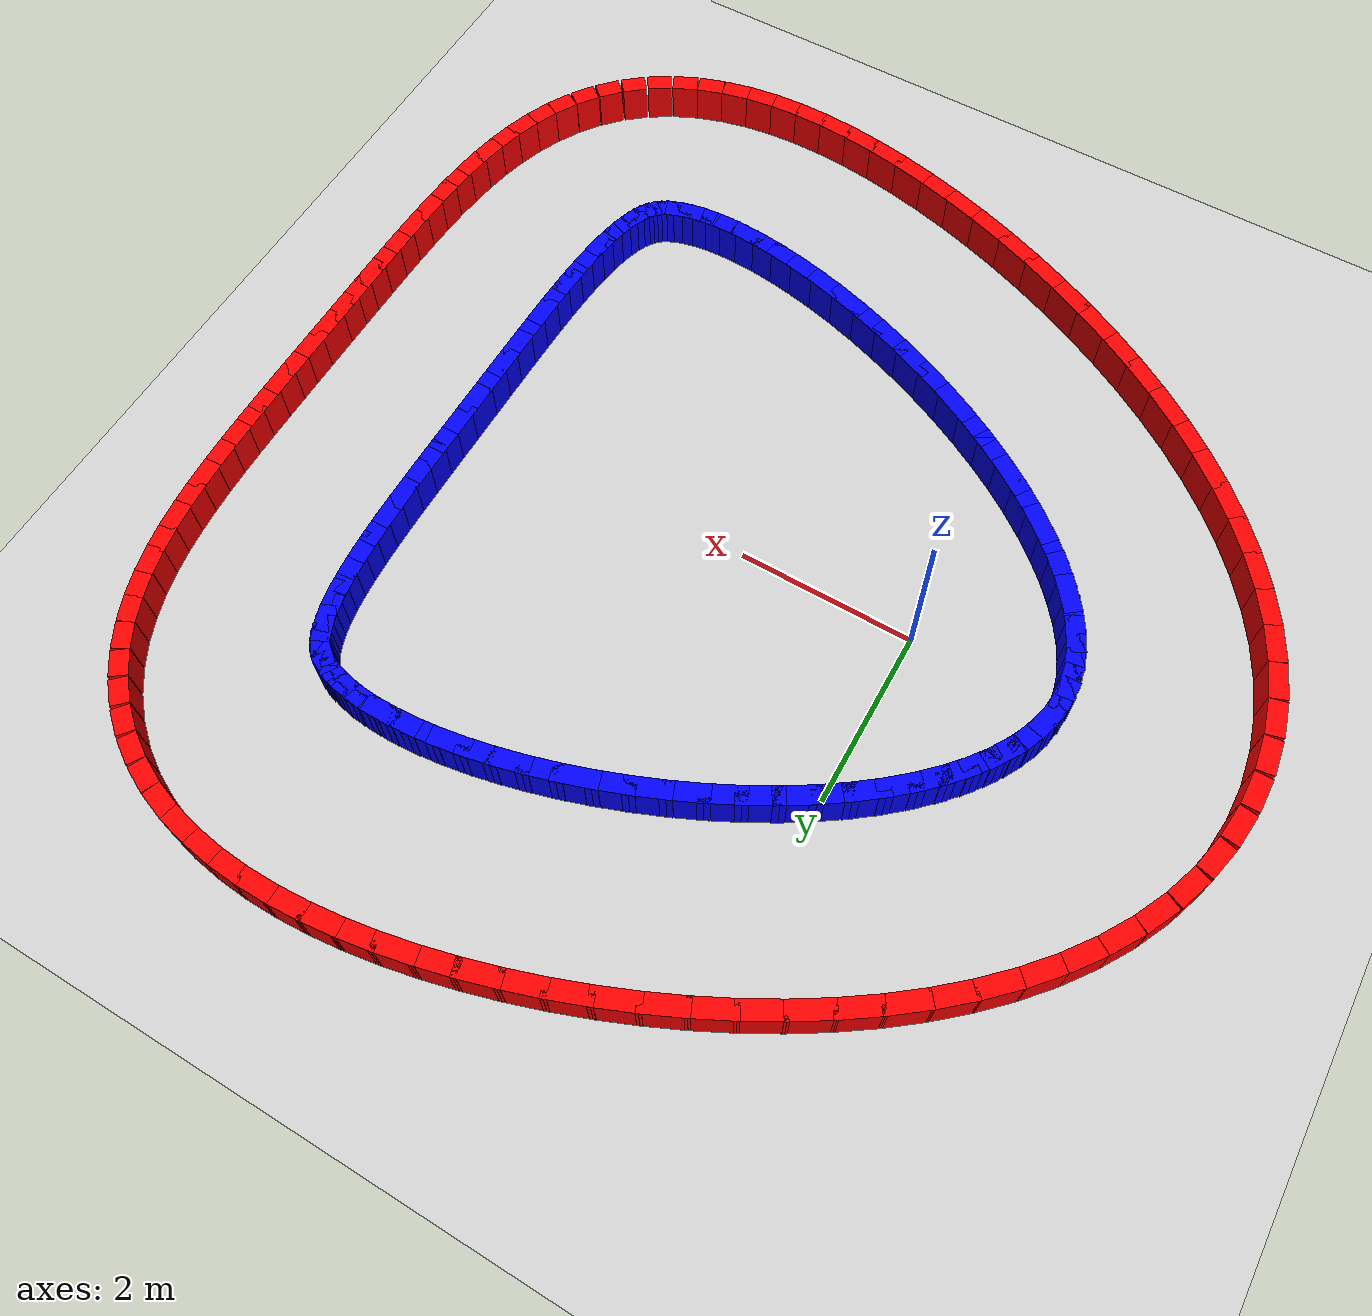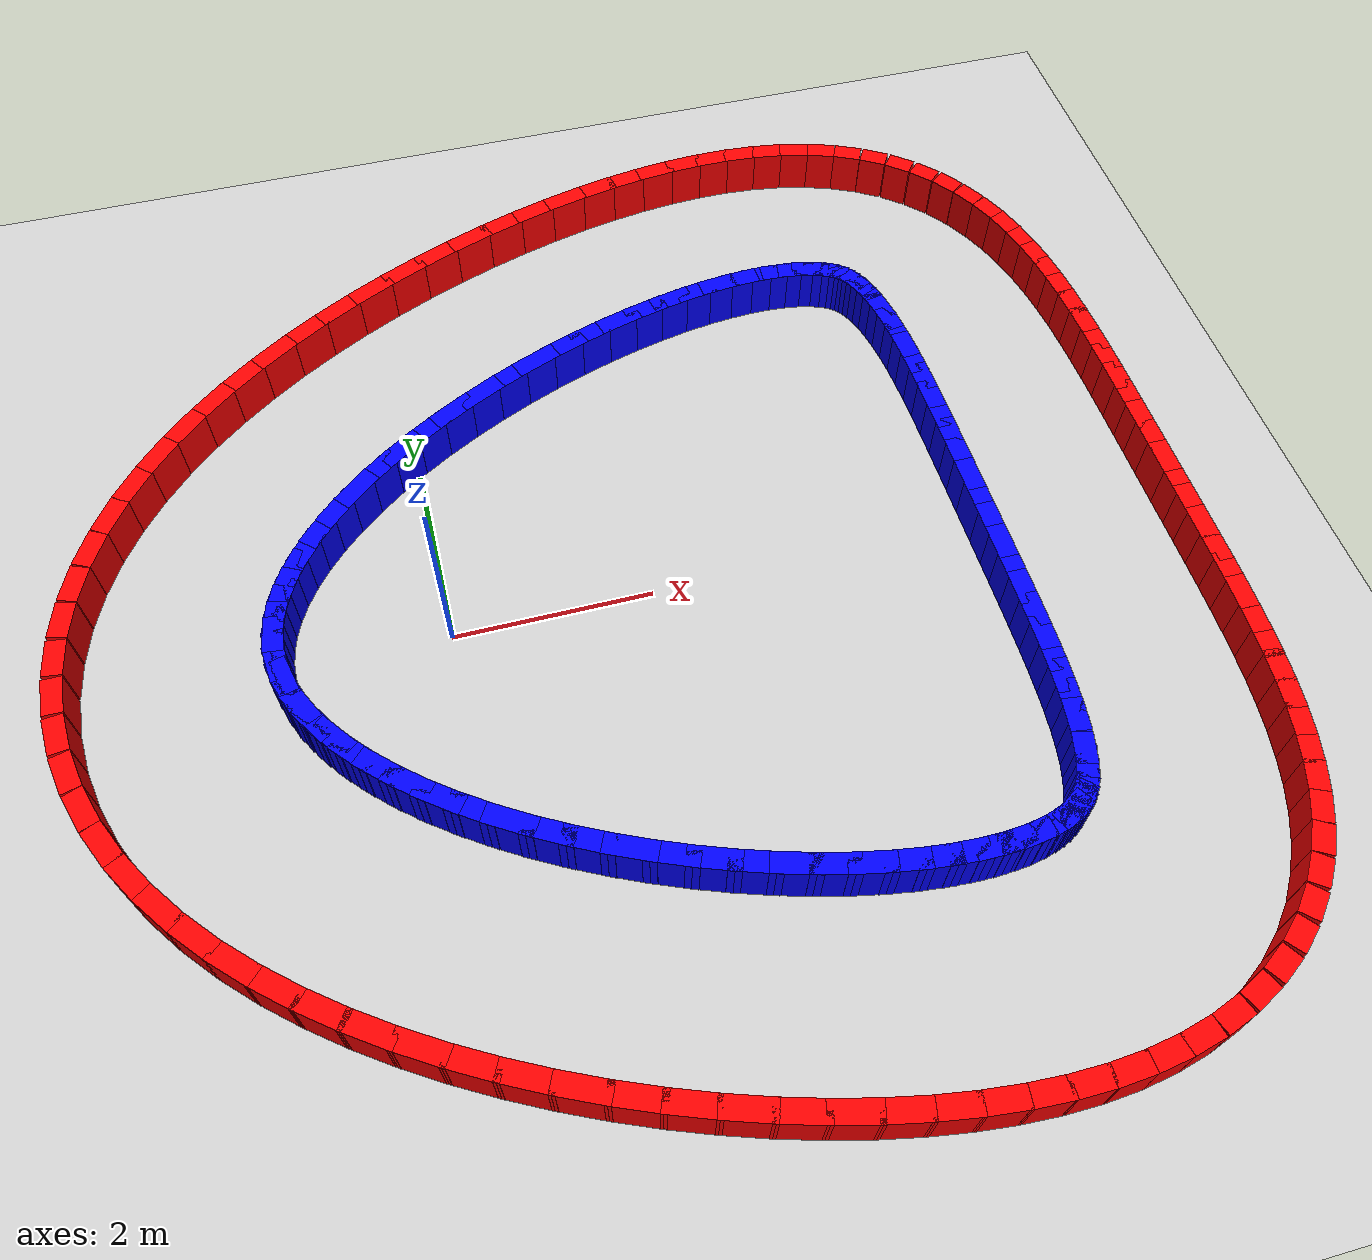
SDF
<?xml version="1.0" ?>
<sdf version="1.9">
  <world name="kidney_track">
    <plugin filename="gz-sim-physics-system" name="gz::sim::systems::Physics"/>
    <plugin filename="gz-sim-user-commands-system" name="gz::sim::systems::UserCommands"/>
    <plugin filename="gz-sim-scene-broadcaster-system" name="gz::sim::systems::SceneBroadcaster"/>
    <plugin filename="gz-sim-sensors-system" name="gz::sim::systems::Sensors">
      <render_engine>ogre2</render_engine>
    </plugin>
    <plugin filename="gz-sim-contact-system" name="gz::sim::systems::Contact"/>

    <gui fullscreen="0">
      <plugin filename="MinimalScene" name="3D View">
        <gz-gui>
          <title>3D View</title>
          <property type="bool" key="showTitleBar">false</property>
          <property type="string" key="state">docked</property>
        </gz-gui>
        <engine>ogre2</engine>
        <scene>scene</scene>
        <ambient_light>0.4 0.4 0.4</ambient_light>
        <background_color>0.8 0.8 0.8</background_color>
        <camera_pose>-6 0 6 0 0.5 0</camera_pose>
      </plugin>
      <plugin filename="GzSceneManager" name="Scene Manager">
        <gz-gui>
          <property key="resizable" type="bool">false</property>
          <property key="width" type="double">5</property>
          <property key="height" type="double">5</property>
          <property key="state" type="string">floating</property>
          <property key="showTitleBar" type="bool">false</property>
        </gz-gui>
      </plugin>
      <plugin filename="InteractiveViewControl" name="Interactive view control">
        <gz-gui>
          <property key="resizable" type="bool">false</property>
          <property key="width" type="double">5</property>
          <property key="height" type="double">5</property>
          <property key="state" type="string">floating</property>
          <property key="showTitleBar" type="bool">false</property>
        </gz-gui>
      </plugin>
      <plugin filename="CameraTracking" name="Camera Tracking">
        <gz-gui>
          <property key="resizable" type="bool">false</property>
          <property key="width" type="double">5</property>
          <property key="height" type="double">5</property>
          <property key="state" type="string">floating</property>
          <property key="showTitleBar" type="bool">false</property>
        </gz-gui>
      </plugin>
      <plugin filename="WorldControl" name="World control">
        <gz-gui>
          <title>World control</title>
          <property type="bool" key="showTitleBar">false</property>
          <property type="bool" key="resizable">false</property>
          <property type="double" key="height">72</property>
          <property type="double" key="width">121</property>
          <property type="double" key="z">1</property>
          <property type="string" key="state">floating</property>
          <property type="anchors" key="anchors">
            <line own="left" target="left"/>
            <line own="bottom" target="bottom"/>
          </property>
        </gz-gui>
        <play_pause>true</play_pause>
        <step>true</step>
        <start_paused>true</start_paused>
        <use_event>true</use_event>
      </plugin>
      <plugin filename="WorldStats" name="World stats">
        <gz-gui>
          <title>World stats</title>
          <property type="bool" key="showTitleBar">false</property>
          <property type="bool" key="resizable">false</property>
          <property type="double" key="height">110</property>
          <property type="double" key="width">290</property>
          <property type="double" key="z">1</property>
          <property type="string" key="state">floating</property>
          <property type="anchors" key="anchors">
            <line own="right" target="right"/>
            <line own="bottom" target="bottom"/>
          </property>
        </gz-gui>
        <sim_time>true</sim_time>
        <real_time>true</real_time>
        <real_time_factor>true</real_time_factor>
        <iterations>true</iterations>
      </plugin>
      <plugin filename="EntityTree" name="Entity tree">
        <gz-gui>
          <property type="string" key="state">docked_collapsed</property>
        </gz-gui>
      </plugin>
    </gui>

    <light type="directional" name="sun">
      <cast_shadows>true</cast_shadows>
      <pose>0 0 10 0 0 0</pose>
      <diffuse>0.8 0.8 0.8 1</diffuse>
      <specular>0.2 0.2 0.2 1</specular>
      <attenuation><range>1000</range><constant>0.9</constant><linear>0.01</linear><quadratic>0.001</quadratic></attenuation>
      <direction>-0.5 0.1 -0.9</direction>
    </light>

    <model name="ground_plane">
      <static>true</static>
      <link name="link">
        <collision name="collision"><geometry><plane><normal>0 0 1</normal><size>100 100</size></plane></geometry></collision>
        <visual name="visual">
          <geometry><plane><normal>0 0 1</normal><size>100 100</size></plane></geometry>
          <material><ambient>0.8 0.8 0.8 1</ambient><diffuse>0.8 0.8 0.8 1</diffuse></material>
        </visual>
      </link>
    </model>

    <model name="track">
      <static>true</static>

      <!-- Segment 0 -->
      <link name="outer_0">
        <pose>7.3750 0.0000 0.25 0 0 1.5708</pose>
        <collision name="col"><geometry><box><size>0.3826 0.2 0.5</size></box></geometry></collision>
        <visual name="vis"><geometry><box><size>0.3826 0.2 0.5</size></box></geometry><material><ambient>1 0 0 1</ambient></material></visual>
      </link>
      <link name="inner_0">
        <pose>5.3750 0.0000 0.25 0 0 1.5708</pose>
        <collision name="col"><geometry><box><size>0.3826 0.2 0.5</size></box></geometry></collision>
        <visual name="vis"><geometry><box><size>0.3826 0.2 0.5</size></box></geometry><material><ambient>0 0 1 1</ambient></material></visual>
      </link>

      <!-- Segment 1 -->
      <link name="outer_1">
        <pose>7.3750 0.2827 0.25 0 0 1.5709</pose>
        <collision name="col"><geometry><box><size>0.3814 0.2 0.5</size></box></geometry></collision>
        <visual name="vis"><geometry><box><size>0.3814 0.2 0.5</size></box></geometry><material><ambient>1 0 0 1</ambient></material></visual>
      </link>
      <link name="inner_1">
        <pose>5.3750 0.2824 0.25 0 0 1.5709</pose>
        <collision name="col"><geometry><box><size>0.3814 0.2 0.5</size></box></geometry></collision>
        <visual name="vis"><geometry><box><size>0.3814 0.2 0.5</size></box></geometry><material><ambient>0 0 1 1</ambient></material></visual>
      </link>

      <!-- Segment 2 -->
      <link name="outer_2">
        <pose>7.3749 0.5650 0.25 0 0 1.5718</pose>
        <collision name="col"><geometry><box><size>0.3792 0.2 0.5</size></box></geometry></collision>
        <visual name="vis"><geometry><box><size>0.3792 0.2 0.5</size></box></geometry><material><ambient>1 0 0 1</ambient></material></visual>
      </link>
      <link name="inner_2">
        <pose>5.3749 0.5630 0.25 0 0 1.5718</pose>
        <collision name="col"><geometry><box><size>0.3792 0.2 0.5</size></box></geometry></collision>
        <visual name="vis"><geometry><box><size>0.3792 0.2 0.5</size></box></geometry><material><ambient>0 0 1 1</ambient></material></visual>
      </link>

      <!-- Segment 3 -->
      <link name="outer_3">
        <pose>7.3743 0.8466 0.25 0 0 1.5742</pose>
        <collision name="col"><geometry><box><size>0.3759 0.2 0.5</size></box></geometry></collision>
        <visual name="vis"><geometry><box><size>0.3759 0.2 0.5</size></box></geometry><material><ambient>1 0 0 1</ambient></material></visual>
      </link>
      <link name="inner_3">
        <pose>5.3743 0.8398 0.25 0 0 1.5742</pose>
        <collision name="col"><geometry><box><size>0.3759 0.2 0.5</size></box></geometry></collision>
        <visual name="vis"><geometry><box><size>0.3759 0.2 0.5</size></box></geometry><material><ambient>0 0 1 1</ambient></material></visual>
      </link>

      <!-- Segment 4 -->
      <link name="outer_4">
        <pose>7.3727 1.1272 0.25 0 0 1.5789</pose>
        <collision name="col"><geometry><box><size>0.3715 0.2 0.5</size></box></geometry></collision>
        <visual name="vis"><geometry><box><size>0.3715 0.2 0.5</size></box></geometry><material><ambient>1 0 0 1</ambient></material></visual>
      </link>
      <link name="inner_4">
        <pose>5.3728 1.1110 0.25 0 0 1.5789</pose>
        <collision name="col"><geometry><box><size>0.3715 0.2 0.5</size></box></geometry></collision>
        <visual name="vis"><geometry><box><size>0.3715 0.2 0.5</size></box></geometry><material><ambient>0 0 1 1</ambient></material></visual>
      </link>

      <!-- Segment 5 -->
      <link name="outer_5">
        <pose>7.3695 1.4065 0.25 0 0 1.5867</pose>
        <collision name="col"><geometry><box><size>0.3660 0.2 0.5</size></box></geometry></collision>
        <visual name="vis"><geometry><box><size>0.3660 0.2 0.5</size></box></geometry><material><ambient>1 0 0 1</ambient></material></visual>
      </link>
      <link name="inner_5">
        <pose>5.3697 1.3747 0.25 0 0 1.5867</pose>
        <collision name="col"><geometry><box><size>0.3660 0.2 0.5</size></box></geometry></collision>
        <visual name="vis"><geometry><box><size>0.3660 0.2 0.5</size></box></geometry><material><ambient>0 0 1 1</ambient></material></visual>
      </link>

      <!-- Segment 6 -->
      <link name="outer_6">
        <pose>7.3635 1.6844 0.25 0 0 1.5986</pose>
        <collision name="col"><geometry><box><size>0.3596 0.2 0.5</size></box></geometry></collision>
        <visual name="vis"><geometry><box><size>0.3596 0.2 0.5</size></box></geometry><material><ambient>1 0 0 1</ambient></material></visual>
      </link>
      <link name="inner_6">
        <pose>5.3643 1.6287 0.25 0 0 1.5986</pose>
        <collision name="col"><geometry><box><size>0.3596 0.2 0.5</size></box></geometry></collision>
        <visual name="vis"><geometry><box><size>0.3596 0.2 0.5</size></box></geometry><material><ambient>0 0 1 1</ambient></material></visual>
      </link>

      <!-- Segment 7 -->
      <link name="outer_7">
        <pose>7.3536 1.9608 0.25 0 0 1.6156</pose>
        <collision name="col"><geometry><box><size>0.3523 0.2 0.5</size></box></geometry></collision>
        <visual name="vis"><geometry><box><size>0.3523 0.2 0.5</size></box></geometry><material><ambient>1 0 0 1</ambient></material></visual>
      </link>
      <link name="inner_7">
        <pose>5.3556 1.8712 0.25 0 0 1.6156</pose>
        <collision name="col"><geometry><box><size>0.3523 0.2 0.5</size></box></geometry></collision>
        <visual name="vis"><geometry><box><size>0.3523 0.2 0.5</size></box></geometry><material><ambient>0 0 1 1</ambient></material></visual>
      </link>

      <!-- Segment 8 -->
      <link name="outer_8">
        <pose>7.3383 2.2358 0.25 0 0 1.6387</pose>
        <collision name="col"><geometry><box><size>0.3442 0.2 0.5</size></box></geometry></collision>
        <visual name="vis"><geometry><box><size>0.3442 0.2 0.5</size></box></geometry><material><ambient>1 0 0 1</ambient></material></visual>
      </link>
      <link name="inner_8">
        <pose>5.3429 2.1000 0.25 0 0 1.6387</pose>
        <collision name="col"><geometry><box><size>0.3442 0.2 0.5</size></box></geometry></collision>
        <visual name="vis"><geometry><box><size>0.3442 0.2 0.5</size></box></geometry><material><ambient>0 0 1 1</ambient></material></visual>
      </link>

      <!-- Segment 9 -->
      <link name="outer_9">
        <pose>7.3156 2.5096 0.25 0 0 1.6693</pose>
        <collision name="col"><geometry><box><size>0.3354 0.2 0.5</size></box></geometry></collision>
        <visual name="vis"><geometry><box><size>0.3354 0.2 0.5</size></box></geometry><material><ambient>1 0 0 1</ambient></material></visual>
      </link>
      <link name="inner_9">
        <pose>5.3253 2.3129 0.25 0 0 1.6693</pose>
        <collision name="col"><geometry><box><size>0.3354 0.2 0.5</size></box></geometry></collision>
        <visual name="vis"><geometry><box><size>0.3354 0.2 0.5</size></box></geometry><material><ambient>0 0 1 1</ambient></material></visual>
      </link>

      <!-- Segment 10 -->
      <link name="outer_10">
        <pose>7.2834 2.7825 0.25 0 0 1.7087</pose>
        <collision name="col"><geometry><box><size>0.3263 0.2 0.5</size></box></geometry></collision>
        <visual name="vis"><geometry><box><size>0.3263 0.2 0.5</size></box></geometry><material><ambient>1 0 0 1</ambient></material></visual>
      </link>
      <link name="inner_10">
        <pose>5.3024 2.5076 0.25 0 0 1.7087</pose>
        <collision name="col"><geometry><box><size>0.3263 0.2 0.5</size></box></geometry></collision>
        <visual name="vis"><geometry><box><size>0.3263 0.2 0.5</size></box></geometry><material><ambient>0 0 1 1</ambient></material></visual>
      </link>

      <!-- Segment 11 -->
      <link name="outer_11">
        <pose>7.2390 3.0550 0.25 0 0 1.7584</pose>
        <collision name="col"><geometry><box><size>0.3172 0.2 0.5</size></box></geometry></collision>
        <visual name="vis"><geometry><box><size>0.3172 0.2 0.5</size></box></geometry><material><ambient>1 0 0 1</ambient></material></visual>
      </link>
      <link name="inner_11">
        <pose>5.2741 2.6819 0.25 0 0 1.7584</pose>
        <collision name="col"><geometry><box><size>0.3172 0.2 0.5</size></box></geometry></collision>
        <visual name="vis"><geometry><box><size>0.3172 0.2 0.5</size></box></geometry><material><ambient>0 0 1 1</ambient></material></visual>
      </link>

      <!-- Segment 12 -->
      <link name="outer_12">
        <pose>7.1788 3.3271 0.25 0 0 1.8201</pose>
        <collision name="col"><geometry><box><size>0.3083 0.2 0.5</size></box></geometry></collision>
        <visual name="vis"><geometry><box><size>0.3083 0.2 0.5</size></box></geometry><material><ambient>1 0 0 1</ambient></material></visual>
      </link>
      <link name="inner_12">
        <pose>5.2406 2.8338 0.25 0 0 1.8201</pose>
        <collision name="col"><geometry><box><size>0.3083 0.2 0.5</size></box></geometry></collision>
        <visual name="vis"><geometry><box><size>0.3083 0.2 0.5</size></box></geometry><material><ambient>0 0 1 1</ambient></material></visual>
      </link>

      <!-- Segment 13 -->
      <link name="outer_13">
        <pose>7.0990 3.5988 0.25 0 0 1.8949</pose>
        <collision name="col"><geometry><box><size>0.3003 0.2 0.5</size></box></geometry></collision>
        <visual name="vis"><geometry><box><size>0.3003 0.2 0.5</size></box></geometry><material><ambient>1 0 0 1</ambient></material></visual>
      </link>
      <link name="inner_13">
        <pose>5.2032 2.9619 0.25 0 0 1.8949</pose>
        <collision name="col"><geometry><box><size>0.3003 0.2 0.5</size></box></geometry></collision>
        <visual name="vis"><geometry><box><size>0.3003 0.2 0.5</size></box></geometry><material><ambient>0 0 1 1</ambient></material></visual>
      </link>

      <!-- Segment 14 -->
      <link name="outer_14">
        <pose>6.9951 3.8688 0.25 0 0 1.9839</pose>
        <collision name="col"><geometry><box><size>0.2937 0.2 0.5</size></box></geometry></collision>
        <visual name="vis"><geometry><box><size>0.2937 0.2 0.5</size></box></geometry><material><ambient>1 0 0 1</ambient></material></visual>
      </link>
      <link name="inner_14">
        <pose>5.1633 3.0659 0.25 0 0 1.9839</pose>
        <collision name="col"><geometry><box><size>0.2937 0.2 0.5</size></box></geometry></collision>
        <visual name="vis"><geometry><box><size>0.2937 0.2 0.5</size></box></geometry><material><ambient>0 0 1 1</ambient></material></visual>
      </link>

      <!-- Segment 15 -->
      <link name="outer_15">
        <pose>6.8624 4.1341 0.25 0 0 2.0869</pose>
        <collision name="col"><geometry><box><size>0.2891 0.2 0.5</size></box></geometry></collision>
        <visual name="vis"><geometry><box><size>0.2891 0.2 0.5</size></box></geometry><material><ambient>1 0 0 1</ambient></material></visual>
      </link>
      <link name="inner_15">
        <pose>5.1229 3.1471 0.25 0 0 2.0869</pose>
        <collision name="col"><geometry><box><size>0.2891 0.2 0.5</size></box></geometry></collision>
        <visual name="vis"><geometry><box><size>0.2891 0.2 0.5</size></box></geometry><material><ambient>0 0 1 1</ambient></material></visual>
      </link>

      <!-- Segment 16 -->
      <link name="outer_16">
        <pose>6.6973 4.3899 0.25 0 0 2.2023</pose>
        <collision name="col"><geometry><box><size>0.2871 0.2 0.5</size></box></geometry></collision>
        <visual name="vis"><geometry><box><size>0.2871 0.2 0.5</size></box></geometry><material><ambient>1 0 0 1</ambient></material></visual>
      </link>
      <link name="inner_16">
        <pose>5.0831 3.2091 0.25 0 0 2.2023</pose>
        <collision name="col"><geometry><box><size>0.2871 0.2 0.5</size></box></geometry></collision>
        <visual name="vis"><geometry><box><size>0.2871 0.2 0.5</size></box></geometry><material><ambient>0 0 1 1</ambient></material></visual>
      </link>

      <!-- Segment 17 -->
      <link name="outer_17">
        <pose>6.4983 4.6293 0.25 0 0 2.3267</pose>
        <collision name="col"><geometry><box><size>0.2882 0.2 0.5</size></box></geometry></collision>
        <visual name="vis"><geometry><box><size>0.2882 0.2 0.5</size></box></geometry><material><ambient>1 0 0 1</ambient></material></visual>
      </link>
      <link name="inner_17">
        <pose>5.0431 3.2574 0.25 0 0 2.3267</pose>
        <collision name="col"><geometry><box><size>0.2882 0.2 0.5</size></box></geometry></collision>
        <visual name="vis"><geometry><box><size>0.2882 0.2 0.5</size></box></geometry><material><ambient>0 0 1 1</ambient></material></visual>
      </link>

      <!-- Segment 18 -->
      <link name="outer_18">
        <pose>6.2669 4.8452 0.25 0 0 2.4551</pose>
        <collision name="col"><geometry><box><size>0.2926 0.2 0.5</size></box></geometry></collision>
        <visual name="vis"><geometry><box><size>0.2926 0.2 0.5</size></box></geometry><material><ambient>1 0 0 1</ambient></material></visual>
      </link>
      <link name="inner_18">
        <pose>4.9993 3.2982 0.25 0 0 2.4551</pose>
        <collision name="col"><geometry><box><size>0.2926 0.2 0.5</size></box></geometry></collision>
        <visual name="vis"><geometry><box><size>0.2926 0.2 0.5</size></box></geometry><material><ambient>0 0 1 1</ambient></material></visual>
      </link>

      <!-- Segment 19 -->
      <link name="outer_19">
        <pose>6.0076 5.0314 0.25 0 0 2.5819</pose>
        <collision name="col"><geometry><box><size>0.3003 0.2 0.5</size></box></geometry></collision>
        <visual name="vis"><geometry><box><size>0.3003 0.2 0.5</size></box></geometry><material><ambient>1 0 0 1</ambient></material></visual>
      </link>
      <link name="inner_19">
        <pose>4.9457 3.3366 0.25 0 0 2.5819</pose>
        <collision name="col"><geometry><box><size>0.3003 0.2 0.5</size></box></geometry></collision>
        <visual name="vis"><geometry><box><size>0.3003 0.2 0.5</size></box></geometry><material><ambient>0 0 1 1</ambient></material></visual>
      </link>

      <!-- Segment 20 -->
      <link name="outer_20">
        <pose>5.7262 5.1847 0.25 0 0 2.7021</pose>
        <collision name="col"><geometry><box><size>0.3111 0.2 0.5</size></box></geometry></collision>
        <visual name="vis"><geometry><box><size>0.3111 0.2 0.5</size></box></geometry><material><ambient>1 0 0 1</ambient></material></visual>
      </link>
      <link name="inner_20">
        <pose>4.8752 3.3748 0.25 0 0 2.7021</pose>
        <collision name="col"><geometry><box><size>0.3111 0.2 0.5</size></box></geometry></collision>
        <visual name="vis"><geometry><box><size>0.3111 0.2 0.5</size></box></geometry><material><ambient>0 0 1 1</ambient></material></visual>
      </link>

      <!-- Segment 21 -->
      <link name="outer_21">
        <pose>5.4283 5.3049 0.25 0 0 2.8123</pose>
        <collision name="col"><geometry><box><size>0.3244 0.2 0.5</size></box></geometry></collision>
        <visual name="vis"><geometry><box><size>0.3244 0.2 0.5</size></box></geometry><material><ambient>1 0 0 1</ambient></material></visual>
      </link>
      <link name="inner_21">
        <pose>4.7816 3.4124 0.25 0 0 2.8123</pose>
        <collision name="col"><geometry><box><size>0.3244 0.2 0.5</size></box></geometry></collision>
        <visual name="vis"><geometry><box><size>0.3244 0.2 0.5</size></box></geometry><material><ambient>0 0 1 1</ambient></material></visual>
      </link>

      <!-- Segment 22 -->
      <link name="outer_22">
        <pose>5.1177 5.3938 0.25 0 0 2.9110</pose>
        <collision name="col"><geometry><box><size>0.3397 0.2 0.5</size></box></geometry></collision>
        <visual name="vis"><geometry><box><size>0.3397 0.2 0.5</size></box></geometry><material><ambient>1 0 0 1</ambient></material></visual>
      </link>
      <link name="inner_22">
        <pose>4.6607 3.4468 0.25 0 0 2.9110</pose>
        <collision name="col"><geometry><box><size>0.3397 0.2 0.5</size></box></geometry></collision>
        <visual name="vis"><geometry><box><size>0.3397 0.2 0.5</size></box></geometry><material><ambient>0 0 1 1</ambient></material></visual>
      </link>

      <!-- Segment 23 -->
      <link name="outer_23">
        <pose>4.7966 5.4542 0.25 0 0 2.9982</pose>
        <collision name="col"><geometry><box><size>0.3564 0.2 0.5</size></box></geometry></collision>
        <visual name="vis"><geometry><box><size>0.3564 0.2 0.5</size></box></geometry><material><ambient>1 0 0 1</ambient></material></visual>
      </link>
      <link name="inner_23">
        <pose>4.5107 3.4748 0.25 0 0 2.9982</pose>
        <collision name="col"><geometry><box><size>0.3564 0.2 0.5</size></box></geometry></collision>
        <visual name="vis"><geometry><box><size>0.3564 0.2 0.5</size></box></geometry><material><ambient>0 0 1 1</ambient></material></visual>
      </link>

      <!-- Segment 24 -->
      <link name="outer_24">
        <pose>4.4657 5.4889 0.25 0 0 3.0746</pose>
        <collision name="col"><geometry><box><size>0.3738 0.2 0.5</size></box></geometry></collision>
        <visual name="vis"><geometry><box><size>0.3738 0.2 0.5</size></box></geometry><material><ambient>1 0 0 1</ambient></material></visual>
      </link>
      <link name="inner_24">
        <pose>4.3317 3.4934 0.25 0 0 3.0746</pose>
        <collision name="col"><geometry><box><size>0.3738 0.2 0.5</size></box></geometry></collision>
        <visual name="vis"><geometry><box><size>0.3738 0.2 0.5</size></box></geometry><material><ambient>0 0 1 1</ambient></material></visual>
      </link>

      <!-- Segment 25 -->
      <link name="outer_25">
        <pose>4.1250 5.5000 0.25 0 0 3.1416</pose>
        <collision name="col"><geometry><box><size>0.3916 0.2 0.5</size></box></geometry></collision>
        <visual name="vis"><geometry><box><size>0.3916 0.2 0.5</size></box></geometry><material><ambient>1 0 0 1</ambient></material></visual>
      </link>
      <link name="inner_25">
        <pose>4.1250 3.5000 0.25 0 0 3.1416</pose>
        <collision name="col"><geometry><box><size>0.3916 0.2 0.5</size></box></geometry></collision>
        <visual name="vis"><geometry><box><size>0.3916 0.2 0.5</size></box></geometry><material><ambient>0 0 1 1</ambient></material></visual>
      </link>

      <!-- Segment 26 -->
      <link name="outer_26">
        <pose>3.7745 5.4894 0.25 0 0 -3.0825</pose>
        <collision name="col"><geometry><box><size>0.4091 0.2 0.5</size></box></geometry></collision>
        <visual name="vis"><geometry><box><size>0.4091 0.2 0.5</size></box></geometry><material><ambient>1 0 0 1</ambient></material></visual>
      </link>
      <link name="inner_26">
        <pose>3.8927 3.4929 0.25 0 0 -3.0825</pose>
        <collision name="col"><geometry><box><size>0.4091 0.2 0.5</size></box></geometry></collision>
        <visual name="vis"><geometry><box><size>0.4091 0.2 0.5</size></box></geometry><material><ambient>0 0 1 1</ambient></material></visual>
      </link>

      <!-- Segment 27 -->
      <link name="outer_27">
        <pose>3.4141 5.4583 0.25 0 0 -3.0298</pose>
        <collision name="col"><geometry><box><size>0.4259 0.2 0.5</size></box></geometry></collision>
        <visual name="vis"><geometry><box><size>0.4259 0.2 0.5</size></box></geometry><material><ambient>1 0 0 1</ambient></material></visual>
      </link>
      <link name="inner_27">
        <pose>3.6372 3.4708 0.25 0 0 -3.0298</pose>
        <collision name="col"><geometry><box><size>0.4259 0.2 0.5</size></box></geometry></collision>
        <visual name="vis"><geometry><box><size>0.4259 0.2 0.5</size></box></geometry><material><ambient>0 0 1 1</ambient></material></visual>
      </link>

      <!-- Segment 28 -->
      <link name="outer_28">
        <pose>3.0442 5.4076 0.25 0 0 -2.9823</pose>
        <collision name="col"><geometry><box><size>0.4417 0.2 0.5</size></box></geometry></collision>
        <visual name="vis"><geometry><box><size>0.4417 0.2 0.5</size></box></geometry><material><ambient>1 0 0 1</ambient></material></visual>
      </link>
      <link name="inner_28">
        <pose>3.3614 3.4330 0.25 0 0 -2.9823</pose>
        <collision name="col"><geometry><box><size>0.4417 0.2 0.5</size></box></geometry></collision>
        <visual name="vis"><geometry><box><size>0.4417 0.2 0.5</size></box></geometry><material><ambient>0 0 1 1</ambient></material></visual>
      </link>

      <!-- Segment 29 -->
      <link name="outer_29">
        <pose>2.6653 5.3381 0.25 0 0 -2.9388</pose>
        <collision name="col"><geometry><box><size>0.4560 0.2 0.5</size></box></geometry></collision>
        <visual name="vis"><geometry><box><size>0.4560 0.2 0.5</size></box></geometry><material><ambient>1 0 0 1</ambient></material></visual>
      </link>
      <link name="inner_29">
        <pose>3.0681 3.3791 0.25 0 0 -2.9388</pose>
        <collision name="col"><geometry><box><size>0.4560 0.2 0.5</size></box></geometry></collision>
        <visual name="vis"><geometry><box><size>0.4560 0.2 0.5</size></box></geometry><material><ambient>0 0 1 1</ambient></material></visual>
      </link>

      <!-- Segment 30 -->
      <link name="outer_30">
        <pose>2.2787 5.2503 0.25 0 0 -2.8983</pose>
        <collision name="col"><geometry><box><size>0.4687 0.2 0.5</size></box></geometry></collision>
        <visual name="vis"><geometry><box><size>0.4687 0.2 0.5</size></box></geometry><material><ambient>1 0 0 1</ambient></material></visual>
      </link>
      <link name="inner_30">
        <pose>2.7605 3.3092 0.25 0 0 -2.8983</pose>
        <collision name="col"><geometry><box><size>0.4687 0.2 0.5</size></box></geometry></collision>
        <visual name="vis"><geometry><box><size>0.4687 0.2 0.5</size></box></geometry><material><ambient>0 0 1 1</ambient></material></visual>
      </link>

      <!-- Segment 31 -->
      <link name="outer_31">
        <pose>1.8855 5.1446 0.25 0 0 -2.8599</pose>
        <collision name="col"><geometry><box><size>0.4794 0.2 0.5</size></box></geometry></collision>
        <visual name="vis"><geometry><box><size>0.4794 0.2 0.5</size></box></geometry><material><ambient>1 0 0 1</ambient></material></visual>
      </link>
      <link name="inner_31">
        <pose>2.4415 3.2234 0.25 0 0 -2.8599</pose>
        <collision name="col"><geometry><box><size>0.4794 0.2 0.5</size></box></geometry></collision>
        <visual name="vis"><geometry><box><size>0.4794 0.2 0.5</size></box></geometry><material><ambient>0 0 1 1</ambient></material></visual>
      </link>

      <!-- Segment 32 -->
      <link name="outer_32">
        <pose>1.4877 5.0213 0.25 0 0 -2.8228</pose>
        <collision name="col"><geometry><box><size>0.4880 0.2 0.5</size></box></geometry></collision>
        <visual name="vis"><geometry><box><size>0.4880 0.2 0.5</size></box></geometry><material><ambient>1 0 0 1</ambient></material></visual>
      </link>
      <link name="inner_32">
        <pose>2.1145 3.1221 0.25 0 0 -2.8228</pose>
        <collision name="col"><geometry><box><size>0.4880 0.2 0.5</size></box></geometry></collision>
        <visual name="vis"><geometry><box><size>0.4880 0.2 0.5</size></box></geometry><material><ambient>0 0 1 1</ambient></material></visual>
      </link>

      <!-- Segment 33 -->
      <link name="outer_33">
        <pose>1.0871 4.8809 0.25 0 0 -2.7863</pose>
        <collision name="col"><geometry><box><size>0.4943 0.2 0.5</size></box></geometry></collision>
        <visual name="vis"><geometry><box><size>0.4943 0.2 0.5</size></box></geometry><material><ambient>1 0 0 1</ambient></material></visual>
      </link>
      <link name="inner_33">
        <pose>1.7828 3.0058 0.25 0 0 -2.7863</pose>
        <collision name="col"><geometry><box><size>0.4943 0.2 0.5</size></box></geometry></collision>
        <visual name="vis"><geometry><box><size>0.4943 0.2 0.5</size></box></geometry><material><ambient>0 0 1 1</ambient></material></visual>
      </link>

      <!-- Segment 34 -->
      <link name="outer_34">
        <pose>0.6859 4.7237 0.25 0 0 -2.7497</pose>
        <collision name="col"><geometry><box><size>0.4982 0.2 0.5</size></box></geometry></collision>
        <visual name="vis"><geometry><box><size>0.4982 0.2 0.5</size></box></geometry><material><ambient>1 0 0 1</ambient></material></visual>
      </link>
      <link name="inner_34">
        <pose>1.4497 2.8753 0.25 0 0 -2.7497</pose>
        <collision name="col"><geometry><box><size>0.4982 0.2 0.5</size></box></geometry></collision>
        <visual name="vis"><geometry><box><size>0.4982 0.2 0.5</size></box></geometry><material><ambient>0 0 1 1</ambient></material></visual>
      </link>

      <!-- Segment 35 -->
      <link name="outer_35">
        <pose>0.2865 4.5499 0.25 0 0 -2.7124</pose>
        <collision name="col"><geometry><box><size>0.4997 0.2 0.5</size></box></geometry></collision>
        <visual name="vis"><geometry><box><size>0.4997 0.2 0.5</size></box></geometry><material><ambient>1 0 0 1</ambient></material></visual>
      </link>
      <link name="inner_35">
        <pose>1.1187 2.7313 0.25 0 0 -2.7124</pose>
        <collision name="col"><geometry><box><size>0.4997 0.2 0.5</size></box></geometry></collision>
        <visual name="vis"><geometry><box><size>0.4997 0.2 0.5</size></box></geometry><material><ambient>0 0 1 1</ambient></material></visual>
      </link>

      <!-- Segment 36 -->
      <link name="outer_36">
        <pose>-0.1086 4.3599 0.25 0 0 -2.6738</pose>
        <collision name="col"><geometry><box><size>0.4988 0.2 0.5</size></box></geometry></collision>
        <visual name="vis"><geometry><box><size>0.4988 0.2 0.5</size></box></geometry><material><ambient>1 0 0 1</ambient></material></visual>
      </link>
      <link name="inner_36">
        <pose>0.7933 2.5748 0.25 0 0 -2.6738</pose>
        <collision name="col"><geometry><box><size>0.4988 0.2 0.5</size></box></geometry></collision>
        <visual name="vis"><geometry><box><size>0.4988 0.2 0.5</size></box></geometry><material><ambient>0 0 1 1</ambient></material></visual>
      </link>

      <!-- Segment 37 -->
      <link name="outer_37">
        <pose>-0.4967 4.1538 0.25 0 0 -2.6330</pose>
        <collision name="col"><geometry><box><size>0.4954 0.2 0.5</size></box></geometry></collision>
        <visual name="vis"><geometry><box><size>0.4954 0.2 0.5</size></box></geometry><material><ambient>1 0 0 1</ambient></material></visual>
      </link>
      <link name="inner_37">
        <pose>0.4771 2.4069 0.25 0 0 -2.6330</pose>
        <collision name="col"><geometry><box><size>0.4954 0.2 0.5</size></box></geometry></collision>
        <visual name="vis"><geometry><box><size>0.4954 0.2 0.5</size></box></geometry><material><ambient>0 0 1 1</ambient></material></visual>
      </link>

      <!-- Segment 38 -->
      <link name="outer_38">
        <pose>-0.8754 3.9319 0.25 0 0 -2.5895</pose>
        <collision name="col"><geometry><box><size>0.4898 0.2 0.5</size></box></geometry></collision>
        <visual name="vis"><geometry><box><size>0.4898 0.2 0.5</size></box></geometry><material><ambient>1 0 0 1</ambient></material></visual>
      </link>
      <link name="inner_38">
        <pose>0.1734 2.2290 0.25 0 0 -2.5895</pose>
        <collision name="col"><geometry><box><size>0.4898 0.2 0.5</size></box></geometry></collision>
        <visual name="vis"><geometry><box><size>0.4898 0.2 0.5</size></box></geometry><material><ambient>0 0 1 1</ambient></material></visual>
      </link>

      <!-- Segment 39 -->
      <link name="outer_39">
        <pose>-1.2420 3.6943 0.25 0 0 -2.5425</pose>
        <collision name="col"><geometry><box><size>0.4822 0.2 0.5</size></box></geometry></collision>
        <visual name="vis"><geometry><box><size>0.4822 0.2 0.5</size></box></geometry><material><ambient>1 0 0 1</ambient></material></visual>
      </link>
      <link name="inner_39">
        <pose>-0.1143 2.0425 0.25 0 0 -2.5425</pose>
        <collision name="col"><geometry><box><size>0.4822 0.2 0.5</size></box></geometry></collision>
        <visual name="vis"><geometry><box><size>0.4822 0.2 0.5</size></box></geometry><material><ambient>0 0 1 1</ambient></material></visual>
      </link>

      <!-- Segment 40 -->
      <link name="outer_40">
        <pose>-1.5937 3.4409 0.25 0 0 -2.4912</pose>
        <collision name="col"><geometry><box><size>0.4727 0.2 0.5</size></box></geometry></collision>
        <visual name="vis"><geometry><box><size>0.4727 0.2 0.5</size></box></geometry><material><ambient>1 0 0 1</ambient></material></visual>
      </link>
      <link name="inner_40">
        <pose>-0.3827 1.8492 0.25 0 0 -2.4912</pose>
        <collision name="col"><geometry><box><size>0.4727 0.2 0.5</size></box></geometry></collision>
        <visual name="vis"><geometry><box><size>0.4727 0.2 0.5</size></box></geometry><material><ambient>0 0 1 1</ambient></material></visual>
      </link>

      <!-- Segment 41 -->
      <link name="outer_41">
        <pose>-1.9281 3.1715 0.25 0 0 -2.4346</pose>
        <collision name="col"><geometry><box><size>0.4618 0.2 0.5</size></box></geometry></collision>
        <visual name="vis"><geometry><box><size>0.4618 0.2 0.5</size></box></geometry><material><ambient>1 0 0 1</ambient></material></visual>
      </link>
      <link name="inner_41">
        <pose>-0.6289 1.6509 0.25 0 0 -2.4346</pose>
        <collision name="col"><geometry><box><size>0.4618 0.2 0.5</size></box></geometry></collision>
        <visual name="vis"><geometry><box><size>0.4618 0.2 0.5</size></box></geometry><material><ambient>0 0 1 1</ambient></material></visual>
      </link>

      <!-- Segment 42 -->
      <link name="outer_42">
        <pose>-2.2422 2.8859 0.25 0 0 -2.3717</pose>
        <collision name="col"><geometry><box><size>0.4497 0.2 0.5</size></box></geometry></collision>
        <visual name="vis"><geometry><box><size>0.4497 0.2 0.5</size></box></geometry><material><ambient>1 0 0 1</ambient></material></visual>
      </link>
      <link name="inner_42">
        <pose>-0.8501 1.4499 0.25 0 0 -2.3717</pose>
        <collision name="col"><geometry><box><size>0.4497 0.2 0.5</size></box></geometry></collision>
        <visual name="vis"><geometry><box><size>0.4497 0.2 0.5</size></box></geometry><material><ambient>0 0 1 1</ambient></material></visual>
      </link>

      <!-- Segment 43 -->
      <link name="outer_43">
        <pose>-2.5335 2.5835 0.25 0 0 -2.3016</pose>
        <collision name="col"><geometry><box><size>0.4371 0.2 0.5</size></box></geometry></collision>
        <visual name="vis"><geometry><box><size>0.4371 0.2 0.5</size></box></geometry><material><ambient>1 0 0 1</ambient></material></visual>
      </link>
      <link name="inner_43">
        <pose>-1.0442 1.2486 0.25 0 0 -2.3016</pose>
        <collision name="col"><geometry><box><size>0.4371 0.2 0.5</size></box></geometry></collision>
        <visual name="vis"><geometry><box><size>0.4371 0.2 0.5</size></box></geometry><material><ambient>0 0 1 1</ambient></material></visual>
      </link>

      <!-- Segment 44 -->
      <link name="outer_44">
        <pose>-2.7987 2.2637 0.25 0 0 -2.2232</pose>
        <collision name="col"><geometry><box><size>0.4245 0.2 0.5</size></box></geometry></collision>
        <visual name="vis"><geometry><box><size>0.4245 0.2 0.5</size></box></geometry><material><ambient>1 0 0 1</ambient></material></visual>
      </link>
      <link name="inner_44">
        <pose>-1.2095 1.0494 0.25 0 0 -2.2232</pose>
        <collision name="col"><geometry><box><size>0.4245 0.2 0.5</size></box></geometry></collision>
        <visual name="vis"><geometry><box><size>0.4245 0.2 0.5</size></box></geometry><material><ambient>0 0 1 1</ambient></material></visual>
      </link>

      <!-- Segment 45 -->
      <link name="outer_45">
        <pose>-3.0345 1.9260 0.25 0 0 -2.1358</pose>
        <collision name="col"><geometry><box><size>0.4124 0.2 0.5</size></box></geometry></collision>
        <visual name="vis"><geometry><box><size>0.4124 0.2 0.5</size></box></geometry><material><ambient>1 0 0 1</ambient></material></visual>
      </link>
      <link name="inner_45">
        <pose>-1.3453 0.8552 0.25 0 0 -2.1358</pose>
        <collision name="col"><geometry><box><size>0.4124 0.2 0.5</size></box></geometry></collision>
        <visual name="vis"><geometry><box><size>0.4124 0.2 0.5</size></box></geometry><material><ambient>0 0 1 1</ambient></material></visual>
      </link>

      <!-- Segment 46 -->
      <link name="outer_46">
        <pose>-3.2369 1.5702 0.25 0 0 -2.0388</pose>
        <collision name="col"><geometry><box><size>0.4016 0.2 0.5</size></box></geometry></collision>
        <visual name="vis"><geometry><box><size>0.4016 0.2 0.5</size></box></geometry><material><ambient>1 0 0 1</ambient></material></visual>
      </link>
      <link name="inner_46">
        <pose>-1.4520 0.6680 0.25 0 0 -2.0388</pose>
        <collision name="col"><geometry><box><size>0.4016 0.2 0.5</size></box></geometry></collision>
        <visual name="vis"><geometry><box><size>0.4016 0.2 0.5</size></box></geometry><material><ambient>0 0 1 1</ambient></material></visual>
      </link>

      <!-- Segment 47 -->
      <link name="outer_47">
        <pose>-3.4017 1.1969 0.25 0 0 -1.9323</pose>
        <collision name="col"><geometry><box><size>0.3927 0.2 0.5</size></box></geometry></collision>
        <visual name="vis"><geometry><box><size>0.3927 0.2 0.5</size></box></geometry><material><ambient>1 0 0 1</ambient></material></visual>
      </link>
      <link name="inner_47">
        <pose>-1.5309 0.4895 0.25 0 0 -1.9323</pose>
        <collision name="col"><geometry><box><size>0.3927 0.2 0.5</size></box></geometry></collision>
        <visual name="vis"><geometry><box><size>0.3927 0.2 0.5</size></box></geometry><material><ambient>0 0 1 1</ambient></material></visual>
      </link>

      <!-- Segment 48 -->
      <link name="outer_48">
        <pose>-3.5239 0.8080 0.25 0 0 -1.8173</pose>
        <collision name="col"><geometry><box><size>0.3864 0.2 0.5</size></box></geometry></collision>
        <visual name="vis"><geometry><box><size>0.3864 0.2 0.5</size></box></geometry><material><ambient>1 0 0 1</ambient></material></visual>
      </link>
      <link name="inner_48">
        <pose>-1.5844 0.3200 0.25 0 0 -1.8173</pose>
        <collision name="col"><geometry><box><size>0.3864 0.2 0.5</size></box></geometry></collision>
        <visual name="vis"><geometry><box><size>0.3864 0.2 0.5</size></box></geometry><material><ambient>0 0 1 1</ambient></material></visual>
      </link>

      <!-- Segment 49 -->
      <link name="outer_49">
        <pose>-3.5994 0.4073 0.25 0 0 -1.6958</pose>
        <collision name="col"><geometry><box><size>0.3831 0.2 0.5</size></box></geometry></collision>
        <visual name="vis"><geometry><box><size>0.3831 0.2 0.5</size></box></geometry><material><ambient>1 0 0 1</ambient></material></visual>
      </link>
      <link name="inner_49">
        <pose>-1.6151 0.1578 0.25 0 0 -1.6958</pose>
        <collision name="col"><geometry><box><size>0.3831 0.2 0.5</size></box></geometry></collision>
        <visual name="vis"><geometry><box><size>0.3831 0.2 0.5</size></box></geometry><material><ambient>0 0 1 1</ambient></material></visual>
      </link>

      <!-- Segment 50 -->
      <link name="outer_50">
        <pose>-3.6250 0.0000 0.25 0 0 -1.5708</pose>
        <collision name="col"><geometry><box><size>0.3831 0.2 0.5</size></box></geometry></collision>
        <visual name="vis"><geometry><box><size>0.3831 0.2 0.5</size></box></geometry><material><ambient>1 0 0 1</ambient></material></visual>
      </link>
      <link name="inner_50">
        <pose>-1.6250 0.0000 0.25 0 0 -1.5708</pose>
        <collision name="col"><geometry><box><size>0.3831 0.2 0.5</size></box></geometry></collision>
        <visual name="vis"><geometry><box><size>0.3831 0.2 0.5</size></box></geometry><material><ambient>0 0 1 1</ambient></material></visual>
      </link>

      <!-- Segment 51 -->
      <link name="outer_51">
        <pose>-3.5994 -0.4073 0.25 0 0 -1.4458</pose>
        <collision name="col"><geometry><box><size>0.3864 0.2 0.5</size></box></geometry></collision>
        <visual name="vis"><geometry><box><size>0.3864 0.2 0.5</size></box></geometry><material><ambient>1 0 0 1</ambient></material></visual>
      </link>
      <link name="inner_51">
        <pose>-1.6151 -0.1578 0.25 0 0 -1.4458</pose>
        <collision name="col"><geometry><box><size>0.3864 0.2 0.5</size></box></geometry></collision>
        <visual name="vis"><geometry><box><size>0.3864 0.2 0.5</size></box></geometry><material><ambient>0 0 1 1</ambient></material></visual>
      </link>

      <!-- Segment 52 -->
      <link name="outer_52">
        <pose>-3.5239 -0.8080 0.25 0 0 -1.3243</pose>
        <collision name="col"><geometry><box><size>0.3927 0.2 0.5</size></box></geometry></collision>
        <visual name="vis"><geometry><box><size>0.3927 0.2 0.5</size></box></geometry><material><ambient>1 0 0 1</ambient></material></visual>
      </link>
      <link name="inner_52">
        <pose>-1.5844 -0.3200 0.25 0 0 -1.3243</pose>
        <collision name="col"><geometry><box><size>0.3927 0.2 0.5</size></box></geometry></collision>
        <visual name="vis"><geometry><box><size>0.3927 0.2 0.5</size></box></geometry><material><ambient>0 0 1 1</ambient></material></visual>
      </link>

      <!-- Segment 53 -->
      <link name="outer_53">
        <pose>-3.4017 -1.1969 0.25 0 0 -1.2093</pose>
        <collision name="col"><geometry><box><size>0.4016 0.2 0.5</size></box></geometry></collision>
        <visual name="vis"><geometry><box><size>0.4016 0.2 0.5</size></box></geometry><material><ambient>1 0 0 1</ambient></material></visual>
      </link>
      <link name="inner_53">
        <pose>-1.5309 -0.4895 0.25 0 0 -1.2093</pose>
        <collision name="col"><geometry><box><size>0.4016 0.2 0.5</size></box></geometry></collision>
        <visual name="vis"><geometry><box><size>0.4016 0.2 0.5</size></box></geometry><material><ambient>0 0 1 1</ambient></material></visual>
      </link>

      <!-- Segment 54 -->
      <link name="outer_54">
        <pose>-3.2369 -1.5702 0.25 0 0 -1.1028</pose>
        <collision name="col"><geometry><box><size>0.4124 0.2 0.5</size></box></geometry></collision>
        <visual name="vis"><geometry><box><size>0.4124 0.2 0.5</size></box></geometry><material><ambient>1 0 0 1</ambient></material></visual>
      </link>
      <link name="inner_54">
        <pose>-1.4520 -0.6680 0.25 0 0 -1.1028</pose>
        <collision name="col"><geometry><box><size>0.4124 0.2 0.5</size></box></geometry></collision>
        <visual name="vis"><geometry><box><size>0.4124 0.2 0.5</size></box></geometry><material><ambient>0 0 1 1</ambient></material></visual>
      </link>

      <!-- Segment 55 -->
      <link name="outer_55">
        <pose>-3.0345 -1.9260 0.25 0 0 -1.0058</pose>
        <collision name="col"><geometry><box><size>0.4245 0.2 0.5</size></box></geometry></collision>
        <visual name="vis"><geometry><box><size>0.4245 0.2 0.5</size></box></geometry><material><ambient>1 0 0 1</ambient></material></visual>
      </link>
      <link name="inner_55">
        <pose>-1.3453 -0.8552 0.25 0 0 -1.0058</pose>
        <collision name="col"><geometry><box><size>0.4245 0.2 0.5</size></box></geometry></collision>
        <visual name="vis"><geometry><box><size>0.4245 0.2 0.5</size></box></geometry><material><ambient>0 0 1 1</ambient></material></visual>
      </link>

      <!-- Segment 56 -->
      <link name="outer_56">
        <pose>-2.7987 -2.2637 0.25 0 0 -0.9184</pose>
        <collision name="col"><geometry><box><size>0.4371 0.2 0.5</size></box></geometry></collision>
        <visual name="vis"><geometry><box><size>0.4371 0.2 0.5</size></box></geometry><material><ambient>1 0 0 1</ambient></material></visual>
      </link>
      <link name="inner_56">
        <pose>-1.2095 -1.0494 0.25 0 0 -0.9184</pose>
        <collision name="col"><geometry><box><size>0.4371 0.2 0.5</size></box></geometry></collision>
        <visual name="vis"><geometry><box><size>0.4371 0.2 0.5</size></box></geometry><material><ambient>0 0 1 1</ambient></material></visual>
      </link>

      <!-- Segment 57 -->
      <link name="outer_57">
        <pose>-2.5335 -2.5835 0.25 0 0 -0.8400</pose>
        <collision name="col"><geometry><box><size>0.4497 0.2 0.5</size></box></geometry></collision>
        <visual name="vis"><geometry><box><size>0.4497 0.2 0.5</size></box></geometry><material><ambient>1 0 0 1</ambient></material></visual>
      </link>
      <link name="inner_57">
        <pose>-1.0442 -1.2486 0.25 0 0 -0.8400</pose>
        <collision name="col"><geometry><box><size>0.4497 0.2 0.5</size></box></geometry></collision>
        <visual name="vis"><geometry><box><size>0.4497 0.2 0.5</size></box></geometry><material><ambient>0 0 1 1</ambient></material></visual>
      </link>

      <!-- Segment 58 -->
      <link name="outer_58">
        <pose>-2.2422 -2.8859 0.25 0 0 -0.7699</pose>
        <collision name="col"><geometry><box><size>0.4618 0.2 0.5</size></box></geometry></collision>
        <visual name="vis"><geometry><box><size>0.4618 0.2 0.5</size></box></geometry><material><ambient>1 0 0 1</ambient></material></visual>
      </link>
      <link name="inner_58">
        <pose>-0.8501 -1.4499 0.25 0 0 -0.7699</pose>
        <collision name="col"><geometry><box><size>0.4618 0.2 0.5</size></box></geometry></collision>
        <visual name="vis"><geometry><box><size>0.4618 0.2 0.5</size></box></geometry><material><ambient>0 0 1 1</ambient></material></visual>
      </link>

      <!-- Segment 59 -->
      <link name="outer_59">
        <pose>-1.9281 -3.1715 0.25 0 0 -0.7070</pose>
        <collision name="col"><geometry><box><size>0.4727 0.2 0.5</size></box></geometry></collision>
        <visual name="vis"><geometry><box><size>0.4727 0.2 0.5</size></box></geometry><material><ambient>1 0 0 1</ambient></material></visual>
      </link>
      <link name="inner_59">
        <pose>-0.6289 -1.6509 0.25 0 0 -0.7070</pose>
        <collision name="col"><geometry><box><size>0.4727 0.2 0.5</size></box></geometry></collision>
        <visual name="vis"><geometry><box><size>0.4727 0.2 0.5</size></box></geometry><material><ambient>0 0 1 1</ambient></material></visual>
      </link>

      <!-- Segment 60 -->
      <link name="outer_60">
        <pose>-1.5937 -3.4409 0.25 0 0 -0.6504</pose>
        <collision name="col"><geometry><box><size>0.4822 0.2 0.5</size></box></geometry></collision>
        <visual name="vis"><geometry><box><size>0.4822 0.2 0.5</size></box></geometry><material><ambient>1 0 0 1</ambient></material></visual>
      </link>
      <link name="inner_60">
        <pose>-0.3827 -1.8492 0.25 0 0 -0.6504</pose>
        <collision name="col"><geometry><box><size>0.4822 0.2 0.5</size></box></geometry></collision>
        <visual name="vis"><geometry><box><size>0.4822 0.2 0.5</size></box></geometry><material><ambient>0 0 1 1</ambient></material></visual>
      </link>

      <!-- Segment 61 -->
      <link name="outer_61">
        <pose>-1.2420 -3.6943 0.25 0 0 -0.5991</pose>
        <collision name="col"><geometry><box><size>0.4898 0.2 0.5</size></box></geometry></collision>
        <visual name="vis"><geometry><box><size>0.4898 0.2 0.5</size></box></geometry><material><ambient>1 0 0 1</ambient></material></visual>
      </link>
      <link name="inner_61">
        <pose>-0.1143 -2.0425 0.25 0 0 -0.5991</pose>
        <collision name="col"><geometry><box><size>0.4898 0.2 0.5</size></box></geometry></collision>
        <visual name="vis"><geometry><box><size>0.4898 0.2 0.5</size></box></geometry><material><ambient>0 0 1 1</ambient></material></visual>
      </link>

      <!-- Segment 62 -->
      <link name="outer_62">
        <pose>-0.8754 -3.9319 0.25 0 0 -0.5520</pose>
        <collision name="col"><geometry><box><size>0.4954 0.2 0.5</size></box></geometry></collision>
        <visual name="vis"><geometry><box><size>0.4954 0.2 0.5</size></box></geometry><material><ambient>1 0 0 1</ambient></material></visual>
      </link>
      <link name="inner_62">
        <pose>0.1734 -2.2290 0.25 0 0 -0.5520</pose>
        <collision name="col"><geometry><box><size>0.4954 0.2 0.5</size></box></geometry></collision>
        <visual name="vis"><geometry><box><size>0.4954 0.2 0.5</size></box></geometry><material><ambient>0 0 1 1</ambient></material></visual>
      </link>

      <!-- Segment 63 -->
      <link name="outer_63">
        <pose>-0.4967 -4.1538 0.25 0 0 -0.5086</pose>
        <collision name="col"><geometry><box><size>0.4988 0.2 0.5</size></box></geometry></collision>
        <visual name="vis"><geometry><box><size>0.4988 0.2 0.5</size></box></geometry><material><ambient>1 0 0 1</ambient></material></visual>
      </link>
      <link name="inner_63">
        <pose>0.4771 -2.4069 0.25 0 0 -0.5086</pose>
        <collision name="col"><geometry><box><size>0.4988 0.2 0.5</size></box></geometry></collision>
        <visual name="vis"><geometry><box><size>0.4988 0.2 0.5</size></box></geometry><material><ambient>0 0 1 1</ambient></material></visual>
      </link>

      <!-- Segment 64 -->
      <link name="outer_64">
        <pose>-0.1086 -4.3599 0.25 0 0 -0.4678</pose>
        <collision name="col"><geometry><box><size>0.4997 0.2 0.5</size></box></geometry></collision>
        <visual name="vis"><geometry><box><size>0.4997 0.2 0.5</size></box></geometry><material><ambient>1 0 0 1</ambient></material></visual>
      </link>
      <link name="inner_64">
        <pose>0.7933 -2.5748 0.25 0 0 -0.4678</pose>
        <collision name="col"><geometry><box><size>0.4997 0.2 0.5</size></box></geometry></collision>
        <visual name="vis"><geometry><box><size>0.4997 0.2 0.5</size></box></geometry><material><ambient>0 0 1 1</ambient></material></visual>
      </link>

      <!-- Segment 65 -->
      <link name="outer_65">
        <pose>0.2865 -4.5499 0.25 0 0 -0.4291</pose>
        <collision name="col"><geometry><box><size>0.4982 0.2 0.5</size></box></geometry></collision>
        <visual name="vis"><geometry><box><size>0.4982 0.2 0.5</size></box></geometry><material><ambient>1 0 0 1</ambient></material></visual>
      </link>
      <link name="inner_65">
        <pose>1.1187 -2.7313 0.25 0 0 -0.4291</pose>
        <collision name="col"><geometry><box><size>0.4982 0.2 0.5</size></box></geometry></collision>
        <visual name="vis"><geometry><box><size>0.4982 0.2 0.5</size></box></geometry><material><ambient>0 0 1 1</ambient></material></visual>
      </link>

      <!-- Segment 66 -->
      <link name="outer_66">
        <pose>0.6859 -4.7237 0.25 0 0 -0.3918</pose>
        <collision name="col"><geometry><box><size>0.4943 0.2 0.5</size></box></geometry></collision>
        <visual name="vis"><geometry><box><size>0.4943 0.2 0.5</size></box></geometry><material><ambient>1 0 0 1</ambient></material></visual>
      </link>
      <link name="inner_66">
        <pose>1.4497 -2.8753 0.25 0 0 -0.3918</pose>
        <collision name="col"><geometry><box><size>0.4943 0.2 0.5</size></box></geometry></collision>
        <visual name="vis"><geometry><box><size>0.4943 0.2 0.5</size></box></geometry><material><ambient>0 0 1 1</ambient></material></visual>
      </link>

      <!-- Segment 67 -->
      <link name="outer_67">
        <pose>1.0871 -4.8809 0.25 0 0 -0.3553</pose>
        <collision name="col"><geometry><box><size>0.4880 0.2 0.5</size></box></geometry></collision>
        <visual name="vis"><geometry><box><size>0.4880 0.2 0.5</size></box></geometry><material><ambient>1 0 0 1</ambient></material></visual>
      </link>
      <link name="inner_67">
        <pose>1.7828 -3.0058 0.25 0 0 -0.3553</pose>
        <collision name="col"><geometry><box><size>0.4880 0.2 0.5</size></box></geometry></collision>
        <visual name="vis"><geometry><box><size>0.4880 0.2 0.5</size></box></geometry><material><ambient>0 0 1 1</ambient></material></visual>
      </link>

      <!-- Segment 68 -->
      <link name="outer_68">
        <pose>1.4877 -5.0213 0.25 0 0 -0.3188</pose>
        <collision name="col"><geometry><box><size>0.4794 0.2 0.5</size></box></geometry></collision>
        <visual name="vis"><geometry><box><size>0.4794 0.2 0.5</size></box></geometry><material><ambient>1 0 0 1</ambient></material></visual>
      </link>
      <link name="inner_68">
        <pose>2.1145 -3.1221 0.25 0 0 -0.3188</pose>
        <collision name="col"><geometry><box><size>0.4794 0.2 0.5</size></box></geometry></collision>
        <visual name="vis"><geometry><box><size>0.4794 0.2 0.5</size></box></geometry><material><ambient>0 0 1 1</ambient></material></visual>
      </link>

      <!-- Segment 69 -->
      <link name="outer_69">
        <pose>1.8855 -5.1446 0.25 0 0 -0.2817</pose>
        <collision name="col"><geometry><box><size>0.4687 0.2 0.5</size></box></geometry></collision>
        <visual name="vis"><geometry><box><size>0.4687 0.2 0.5</size></box></geometry><material><ambient>1 0 0 1</ambient></material></visual>
      </link>
      <link name="inner_69">
        <pose>2.4415 -3.2234 0.25 0 0 -0.2817</pose>
        <collision name="col"><geometry><box><size>0.4687 0.2 0.5</size></box></geometry></collision>
        <visual name="vis"><geometry><box><size>0.4687 0.2 0.5</size></box></geometry><material><ambient>0 0 1 1</ambient></material></visual>
      </link>

      <!-- Segment 70 -->
      <link name="outer_70">
        <pose>2.2787 -5.2503 0.25 0 0 -0.2433</pose>
        <collision name="col"><geometry><box><size>0.4560 0.2 0.5</size></box></geometry></collision>
        <visual name="vis"><geometry><box><size>0.4560 0.2 0.5</size></box></geometry><material><ambient>1 0 0 1</ambient></material></visual>
      </link>
      <link name="inner_70">
        <pose>2.7605 -3.3092 0.25 0 0 -0.2433</pose>
        <collision name="col"><geometry><box><size>0.4560 0.2 0.5</size></box></geometry></collision>
        <visual name="vis"><geometry><box><size>0.4560 0.2 0.5</size></box></geometry><material><ambient>0 0 1 1</ambient></material></visual>
      </link>

      <!-- Segment 71 -->
      <link name="outer_71">
        <pose>2.6653 -5.3381 0.25 0 0 -0.2028</pose>
        <collision name="col"><geometry><box><size>0.4417 0.2 0.5</size></box></geometry></collision>
        <visual name="vis"><geometry><box><size>0.4417 0.2 0.5</size></box></geometry><material><ambient>1 0 0 1</ambient></material></visual>
      </link>
      <link name="inner_71">
        <pose>3.0681 -3.3791 0.25 0 0 -0.2028</pose>
        <collision name="col"><geometry><box><size>0.4417 0.2 0.5</size></box></geometry></collision>
        <visual name="vis"><geometry><box><size>0.4417 0.2 0.5</size></box></geometry><material><ambient>0 0 1 1</ambient></material></visual>
      </link>

      <!-- Segment 72 -->
      <link name="outer_72">
        <pose>3.0442 -5.4076 0.25 0 0 -0.1593</pose>
        <collision name="col"><geometry><box><size>0.4259 0.2 0.5</size></box></geometry></collision>
        <visual name="vis"><geometry><box><size>0.4259 0.2 0.5</size></box></geometry><material><ambient>1 0 0 1</ambient></material></visual>
      </link>
      <link name="inner_72">
        <pose>3.3614 -3.4330 0.25 0 0 -0.1593</pose>
        <collision name="col"><geometry><box><size>0.4259 0.2 0.5</size></box></geometry></collision>
        <visual name="vis"><geometry><box><size>0.4259 0.2 0.5</size></box></geometry><material><ambient>0 0 1 1</ambient></material></visual>
      </link>

      <!-- Segment 73 -->
      <link name="outer_73">
        <pose>3.4141 -5.4583 0.25 0 0 -0.1118</pose>
        <collision name="col"><geometry><box><size>0.4091 0.2 0.5</size></box></geometry></collision>
        <visual name="vis"><geometry><box><size>0.4091 0.2 0.5</size></box></geometry><material><ambient>1 0 0 1</ambient></material></visual>
      </link>
      <link name="inner_73">
        <pose>3.6372 -3.4708 0.25 0 0 -0.1118</pose>
        <collision name="col"><geometry><box><size>0.4091 0.2 0.5</size></box></geometry></collision>
        <visual name="vis"><geometry><box><size>0.4091 0.2 0.5</size></box></geometry><material><ambient>0 0 1 1</ambient></material></visual>
      </link>

      <!-- Segment 74 -->
      <link name="outer_74">
        <pose>3.7745 -5.4894 0.25 0 0 -0.0591</pose>
        <collision name="col"><geometry><box><size>0.3916 0.2 0.5</size></box></geometry></collision>
        <visual name="vis"><geometry><box><size>0.3916 0.2 0.5</size></box></geometry><material><ambient>1 0 0 1</ambient></material></visual>
      </link>
      <link name="inner_74">
        <pose>3.8927 -3.4929 0.25 0 0 -0.0591</pose>
        <collision name="col"><geometry><box><size>0.3916 0.2 0.5</size></box></geometry></collision>
        <visual name="vis"><geometry><box><size>0.3916 0.2 0.5</size></box></geometry><material><ambient>0 0 1 1</ambient></material></visual>
      </link>

      <!-- Segment 75 -->
      <link name="outer_75">
        <pose>4.1250 -5.5000 0.25 0 0 0.0000</pose>
        <collision name="col"><geometry><box><size>0.3738 0.2 0.5</size></box></geometry></collision>
        <visual name="vis"><geometry><box><size>0.3738 0.2 0.5</size></box></geometry><material><ambient>1 0 0 1</ambient></material></visual>
      </link>
      <link name="inner_75">
        <pose>4.1250 -3.5000 0.25 0 0 0.0000</pose>
        <collision name="col"><geometry><box><size>0.3738 0.2 0.5</size></box></geometry></collision>
        <visual name="vis"><geometry><box><size>0.3738 0.2 0.5</size></box></geometry><material><ambient>0 0 1 1</ambient></material></visual>
      </link>

      <!-- Segment 76 -->
      <link name="outer_76">
        <pose>4.4657 -5.4889 0.25 0 0 0.0670</pose>
        <collision name="col"><geometry><box><size>0.3564 0.2 0.5</size></box></geometry></collision>
        <visual name="vis"><geometry><box><size>0.3564 0.2 0.5</size></box></geometry><material><ambient>1 0 0 1</ambient></material></visual>
      </link>
      <link name="inner_76">
        <pose>4.3317 -3.4934 0.25 0 0 0.0670</pose>
        <collision name="col"><geometry><box><size>0.3564 0.2 0.5</size></box></geometry></collision>
        <visual name="vis"><geometry><box><size>0.3564 0.2 0.5</size></box></geometry><material><ambient>0 0 1 1</ambient></material></visual>
      </link>

      <!-- Segment 77 -->
      <link name="outer_77">
        <pose>4.7966 -5.4542 0.25 0 0 0.1434</pose>
        <collision name="col"><geometry><box><size>0.3397 0.2 0.5</size></box></geometry></collision>
        <visual name="vis"><geometry><box><size>0.3397 0.2 0.5</size></box></geometry><material><ambient>1 0 0 1</ambient></material></visual>
      </link>
      <link name="inner_77">
        <pose>4.5107 -3.4748 0.25 0 0 0.1434</pose>
        <collision name="col"><geometry><box><size>0.3397 0.2 0.5</size></box></geometry></collision>
        <visual name="vis"><geometry><box><size>0.3397 0.2 0.5</size></box></geometry><material><ambient>0 0 1 1</ambient></material></visual>
      </link>

      <!-- Segment 78 -->
      <link name="outer_78">
        <pose>5.1177 -5.3938 0.25 0 0 0.2306</pose>
        <collision name="col"><geometry><box><size>0.3244 0.2 0.5</size></box></geometry></collision>
        <visual name="vis"><geometry><box><size>0.3244 0.2 0.5</size></box></geometry><material><ambient>1 0 0 1</ambient></material></visual>
      </link>
      <link name="inner_78">
        <pose>4.6607 -3.4468 0.25 0 0 0.2306</pose>
        <collision name="col"><geometry><box><size>0.3244 0.2 0.5</size></box></geometry></collision>
        <visual name="vis"><geometry><box><size>0.3244 0.2 0.5</size></box></geometry><material><ambient>0 0 1 1</ambient></material></visual>
      </link>

      <!-- Segment 79 -->
      <link name="outer_79">
        <pose>5.4283 -5.3049 0.25 0 0 0.3293</pose>
        <collision name="col"><geometry><box><size>0.3111 0.2 0.5</size></box></geometry></collision>
        <visual name="vis"><geometry><box><size>0.3111 0.2 0.5</size></box></geometry><material><ambient>1 0 0 1</ambient></material></visual>
      </link>
      <link name="inner_79">
        <pose>4.7816 -3.4124 0.25 0 0 0.3293</pose>
        <collision name="col"><geometry><box><size>0.3111 0.2 0.5</size></box></geometry></collision>
        <visual name="vis"><geometry><box><size>0.3111 0.2 0.5</size></box></geometry><material><ambient>0 0 1 1</ambient></material></visual>
      </link>

      <!-- Segment 80 -->
      <link name="outer_80">
        <pose>5.7262 -5.1847 0.25 0 0 0.4395</pose>
        <collision name="col"><geometry><box><size>0.3003 0.2 0.5</size></box></geometry></collision>
        <visual name="vis"><geometry><box><size>0.3003 0.2 0.5</size></box></geometry><material><ambient>1 0 0 1</ambient></material></visual>
      </link>
      <link name="inner_80">
        <pose>4.8752 -3.3748 0.25 0 0 0.4395</pose>
        <collision name="col"><geometry><box><size>0.3003 0.2 0.5</size></box></geometry></collision>
        <visual name="vis"><geometry><box><size>0.3003 0.2 0.5</size></box></geometry><material><ambient>0 0 1 1</ambient></material></visual>
      </link>

      <!-- Segment 81 -->
      <link name="outer_81">
        <pose>6.0076 -5.0314 0.25 0 0 0.5597</pose>
        <collision name="col"><geometry><box><size>0.2926 0.2 0.5</size></box></geometry></collision>
        <visual name="vis"><geometry><box><size>0.2926 0.2 0.5</size></box></geometry><material><ambient>1 0 0 1</ambient></material></visual>
      </link>
      <link name="inner_81">
        <pose>4.9457 -3.3366 0.25 0 0 0.5597</pose>
        <collision name="col"><geometry><box><size>0.2926 0.2 0.5</size></box></geometry></collision>
        <visual name="vis"><geometry><box><size>0.2926 0.2 0.5</size></box></geometry><material><ambient>0 0 1 1</ambient></material></visual>
      </link>

      <!-- Segment 82 -->
      <link name="outer_82">
        <pose>6.2669 -4.8452 0.25 0 0 0.6865</pose>
        <collision name="col"><geometry><box><size>0.2882 0.2 0.5</size></box></geometry></collision>
        <visual name="vis"><geometry><box><size>0.2882 0.2 0.5</size></box></geometry><material><ambient>1 0 0 1</ambient></material></visual>
      </link>
      <link name="inner_82">
        <pose>4.9993 -3.2982 0.25 0 0 0.6865</pose>
        <collision name="col"><geometry><box><size>0.2882 0.2 0.5</size></box></geometry></collision>
        <visual name="vis"><geometry><box><size>0.2882 0.2 0.5</size></box></geometry><material><ambient>0 0 1 1</ambient></material></visual>
      </link>

      <!-- Segment 83 -->
      <link name="outer_83">
        <pose>6.4983 -4.6293 0.25 0 0 0.8149</pose>
        <collision name="col"><geometry><box><size>0.2871 0.2 0.5</size></box></geometry></collision>
        <visual name="vis"><geometry><box><size>0.2871 0.2 0.5</size></box></geometry><material><ambient>1 0 0 1</ambient></material></visual>
      </link>
      <link name="inner_83">
        <pose>5.0431 -3.2574 0.25 0 0 0.8149</pose>
        <collision name="col"><geometry><box><size>0.2871 0.2 0.5</size></box></geometry></collision>
        <visual name="vis"><geometry><box><size>0.2871 0.2 0.5</size></box></geometry><material><ambient>0 0 1 1</ambient></material></visual>
      </link>

      <!-- Segment 84 -->
      <link name="outer_84">
        <pose>6.6973 -4.3899 0.25 0 0 0.9393</pose>
        <collision name="col"><geometry><box><size>0.2891 0.2 0.5</size></box></geometry></collision>
        <visual name="vis"><geometry><box><size>0.2891 0.2 0.5</size></box></geometry><material><ambient>1 0 0 1</ambient></material></visual>
      </link>
      <link name="inner_84">
        <pose>5.0831 -3.2091 0.25 0 0 0.9393</pose>
        <collision name="col"><geometry><box><size>0.2891 0.2 0.5</size></box></geometry></collision>
        <visual name="vis"><geometry><box><size>0.2891 0.2 0.5</size></box></geometry><material><ambient>0 0 1 1</ambient></material></visual>
      </link>

      <!-- Segment 85 -->
      <link name="outer_85">
        <pose>6.8624 -4.1341 0.25 0 0 1.0547</pose>
        <collision name="col"><geometry><box><size>0.2937 0.2 0.5</size></box></geometry></collision>
        <visual name="vis"><geometry><box><size>0.2937 0.2 0.5</size></box></geometry><material><ambient>1 0 0 1</ambient></material></visual>
      </link>
      <link name="inner_85">
        <pose>5.1229 -3.1471 0.25 0 0 1.0547</pose>
        <collision name="col"><geometry><box><size>0.2937 0.2 0.5</size></box></geometry></collision>
        <visual name="vis"><geometry><box><size>0.2937 0.2 0.5</size></box></geometry><material><ambient>0 0 1 1</ambient></material></visual>
      </link>

      <!-- Segment 86 -->
      <link name="outer_86">
        <pose>6.9951 -3.8688 0.25 0 0 1.1577</pose>
        <collision name="col"><geometry><box><size>0.3003 0.2 0.5</size></box></geometry></collision>
        <visual name="vis"><geometry><box><size>0.3003 0.2 0.5</size></box></geometry><material><ambient>1 0 0 1</ambient></material></visual>
      </link>
      <link name="inner_86">
        <pose>5.1633 -3.0659 0.25 0 0 1.1577</pose>
        <collision name="col"><geometry><box><size>0.3003 0.2 0.5</size></box></geometry></collision>
        <visual name="vis"><geometry><box><size>0.3003 0.2 0.5</size></box></geometry><material><ambient>0 0 1 1</ambient></material></visual>
      </link>

      <!-- Segment 87 -->
      <link name="outer_87">
        <pose>7.0990 -3.5988 0.25 0 0 1.2467</pose>
        <collision name="col"><geometry><box><size>0.3083 0.2 0.5</size></box></geometry></collision>
        <visual name="vis"><geometry><box><size>0.3083 0.2 0.5</size></box></geometry><material><ambient>1 0 0 1</ambient></material></visual>
      </link>
      <link name="inner_87">
        <pose>5.2032 -2.9619 0.25 0 0 1.2467</pose>
        <collision name="col"><geometry><box><size>0.3083 0.2 0.5</size></box></geometry></collision>
        <visual name="vis"><geometry><box><size>0.3083 0.2 0.5</size></box></geometry><material><ambient>0 0 1 1</ambient></material></visual>
      </link>

      <!-- Segment 88 -->
      <link name="outer_88">
        <pose>7.1788 -3.3271 0.25 0 0 1.3215</pose>
        <collision name="col"><geometry><box><size>0.3172 0.2 0.5</size></box></geometry></collision>
        <visual name="vis"><geometry><box><size>0.3172 0.2 0.5</size></box></geometry><material><ambient>1 0 0 1</ambient></material></visual>
      </link>
      <link name="inner_88">
        <pose>5.2406 -2.8338 0.25 0 0 1.3215</pose>
        <collision name="col"><geometry><box><size>0.3172 0.2 0.5</size></box></geometry></collision>
        <visual name="vis"><geometry><box><size>0.3172 0.2 0.5</size></box></geometry><material><ambient>0 0 1 1</ambient></material></visual>
      </link>

      <!-- Segment 89 -->
      <link name="outer_89">
        <pose>7.2390 -3.0550 0.25 0 0 1.3832</pose>
        <collision name="col"><geometry><box><size>0.3263 0.2 0.5</size></box></geometry></collision>
        <visual name="vis"><geometry><box><size>0.3263 0.2 0.5</size></box></geometry><material><ambient>1 0 0 1</ambient></material></visual>
      </link>
      <link name="inner_89">
        <pose>5.2741 -2.6819 0.25 0 0 1.3832</pose>
        <collision name="col"><geometry><box><size>0.3263 0.2 0.5</size></box></geometry></collision>
        <visual name="vis"><geometry><box><size>0.3263 0.2 0.5</size></box></geometry><material><ambient>0 0 1 1</ambient></material></visual>
      </link>

      <!-- Segment 90 -->
      <link name="outer_90">
        <pose>7.2834 -2.7825 0.25 0 0 1.4329</pose>
        <collision name="col"><geometry><box><size>0.3354 0.2 0.5</size></box></geometry></collision>
        <visual name="vis"><geometry><box><size>0.3354 0.2 0.5</size></box></geometry><material><ambient>1 0 0 1</ambient></material></visual>
      </link>
      <link name="inner_90">
        <pose>5.3024 -2.5076 0.25 0 0 1.4329</pose>
        <collision name="col"><geometry><box><size>0.3354 0.2 0.5</size></box></geometry></collision>
        <visual name="vis"><geometry><box><size>0.3354 0.2 0.5</size></box></geometry><material><ambient>0 0 1 1</ambient></material></visual>
      </link>

      <!-- Segment 91 -->
      <link name="outer_91">
        <pose>7.3156 -2.5096 0.25 0 0 1.4723</pose>
        <collision name="col"><geometry><box><size>0.3442 0.2 0.5</size></box></geometry></collision>
        <visual name="vis"><geometry><box><size>0.3442 0.2 0.5</size></box></geometry><material><ambient>1 0 0 1</ambient></material></visual>
      </link>
      <link name="inner_91">
        <pose>5.3253 -2.3129 0.25 0 0 1.4723</pose>
        <collision name="col"><geometry><box><size>0.3442 0.2 0.5</size></box></geometry></collision>
        <visual name="vis"><geometry><box><size>0.3442 0.2 0.5</size></box></geometry><material><ambient>0 0 1 1</ambient></material></visual>
      </link>

      <!-- Segment 92 -->
      <link name="outer_92">
        <pose>7.3383 -2.2358 0.25 0 0 1.5029</pose>
        <collision name="col"><geometry><box><size>0.3523 0.2 0.5</size></box></geometry></collision>
        <visual name="vis"><geometry><box><size>0.3523 0.2 0.5</size></box></geometry><material><ambient>1 0 0 1</ambient></material></visual>
      </link>
      <link name="inner_92">
        <pose>5.3429 -2.1000 0.25 0 0 1.5029</pose>
        <collision name="col"><geometry><box><size>0.3523 0.2 0.5</size></box></geometry></collision>
        <visual name="vis"><geometry><box><size>0.3523 0.2 0.5</size></box></geometry><material><ambient>0 0 1 1</ambient></material></visual>
      </link>

      <!-- Segment 93 -->
      <link name="outer_93">
        <pose>7.3536 -1.9608 0.25 0 0 1.5260</pose>
        <collision name="col"><geometry><box><size>0.3596 0.2 0.5</size></box></geometry></collision>
        <visual name="vis"><geometry><box><size>0.3596 0.2 0.5</size></box></geometry><material><ambient>1 0 0 1</ambient></material></visual>
      </link>
      <link name="inner_93">
        <pose>5.3556 -1.8712 0.25 0 0 1.5260</pose>
        <collision name="col"><geometry><box><size>0.3596 0.2 0.5</size></box></geometry></collision>
        <visual name="vis"><geometry><box><size>0.3596 0.2 0.5</size></box></geometry><material><ambient>0 0 1 1</ambient></material></visual>
      </link>

      <!-- Segment 94 -->
      <link name="outer_94">
        <pose>7.3635 -1.6844 0.25 0 0 1.5430</pose>
        <collision name="col"><geometry><box><size>0.3660 0.2 0.5</size></box></geometry></collision>
        <visual name="vis"><geometry><box><size>0.3660 0.2 0.5</size></box></geometry><material><ambient>1 0 0 1</ambient></material></visual>
      </link>
      <link name="inner_94">
        <pose>5.3643 -1.6287 0.25 0 0 1.5430</pose>
        <collision name="col"><geometry><box><size>0.3660 0.2 0.5</size></box></geometry></collision>
        <visual name="vis"><geometry><box><size>0.3660 0.2 0.5</size></box></geometry><material><ambient>0 0 1 1</ambient></material></visual>
      </link>

      <!-- Segment 95 -->
      <link name="outer_95">
        <pose>7.3695 -1.4065 0.25 0 0 1.5549</pose>
        <collision name="col"><geometry><box><size>0.3715 0.2 0.5</size></box></geometry></collision>
        <visual name="vis"><geometry><box><size>0.3715 0.2 0.5</size></box></geometry><material><ambient>1 0 0 1</ambient></material></visual>
      </link>
      <link name="inner_95">
        <pose>5.3697 -1.3747 0.25 0 0 1.5549</pose>
        <collision name="col"><geometry><box><size>0.3715 0.2 0.5</size></box></geometry></collision>
        <visual name="vis"><geometry><box><size>0.3715 0.2 0.5</size></box></geometry><material><ambient>0 0 1 1</ambient></material></visual>
      </link>

      <!-- Segment 96 -->
      <link name="outer_96">
        <pose>7.3727 -1.1272 0.25 0 0 1.5627</pose>
        <collision name="col"><geometry><box><size>0.3759 0.2 0.5</size></box></geometry></collision>
        <visual name="vis"><geometry><box><size>0.3759 0.2 0.5</size></box></geometry><material><ambient>1 0 0 1</ambient></material></visual>
      </link>
      <link name="inner_96">
        <pose>5.3728 -1.1110 0.25 0 0 1.5627</pose>
        <collision name="col"><geometry><box><size>0.3759 0.2 0.5</size></box></geometry></collision>
        <visual name="vis"><geometry><box><size>0.3759 0.2 0.5</size></box></geometry><material><ambient>0 0 1 1</ambient></material></visual>
      </link>

      <!-- Segment 97 -->
      <link name="outer_97">
        <pose>7.3743 -0.8466 0.25 0 0 1.5674</pose>
        <collision name="col"><geometry><box><size>0.3792 0.2 0.5</size></box></geometry></collision>
        <visual name="vis"><geometry><box><size>0.3792 0.2 0.5</size></box></geometry><material><ambient>1 0 0 1</ambient></material></visual>
      </link>
      <link name="inner_97">
        <pose>5.3743 -0.8398 0.25 0 0 1.5674</pose>
        <collision name="col"><geometry><box><size>0.3792 0.2 0.5</size></box></geometry></collision>
        <visual name="vis"><geometry><box><size>0.3792 0.2 0.5</size></box></geometry><material><ambient>0 0 1 1</ambient></material></visual>
      </link>

      <!-- Segment 98 -->
      <link name="outer_98">
        <pose>7.3749 -0.5650 0.25 0 0 1.5698</pose>
        <collision name="col"><geometry><box><size>0.3814 0.2 0.5</size></box></geometry></collision>
        <visual name="vis"><geometry><box><size>0.3814 0.2 0.5</size></box></geometry><material><ambient>1 0 0 1</ambient></material></visual>
      </link>
      <link name="inner_98">
        <pose>5.3749 -0.5630 0.25 0 0 1.5698</pose>
        <collision name="col"><geometry><box><size>0.3814 0.2 0.5</size></box></geometry></collision>
        <visual name="vis"><geometry><box><size>0.3814 0.2 0.5</size></box></geometry><material><ambient>0 0 1 1</ambient></material></visual>
      </link>

      <!-- Segment 99 -->
      <link name="outer_99">
        <pose>7.3750 -0.2827 0.25 0 0 1.5707</pose>
        <collision name="col"><geometry><box><size>0.3826 0.2 0.5</size></box></geometry></collision>
        <visual name="vis"><geometry><box><size>0.3826 0.2 0.5</size></box></geometry><material><ambient>1 0 0 1</ambient></material></visual>
      </link>
      <link name="inner_99">
        <pose>5.3750 -0.2824 0.25 0 0 1.5707</pose>
        <collision name="col"><geometry><box><size>0.3826 0.2 0.5</size></box></geometry></collision>
        <visual name="vis"><geometry><box><size>0.3826 0.2 0.5</size></box></geometry><material><ambient>0 0 1 1</ambient></material></visual>
      </link>

    </model>
  </world>
</sdf>
